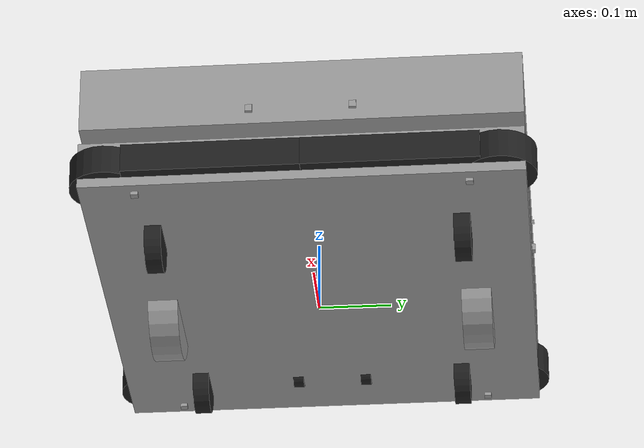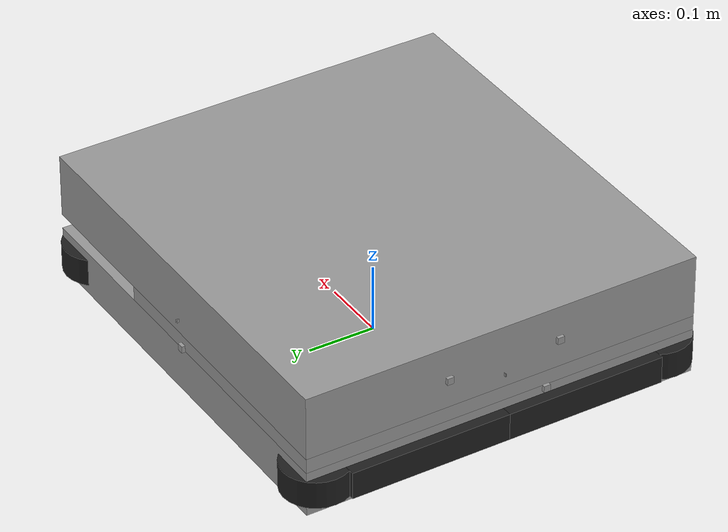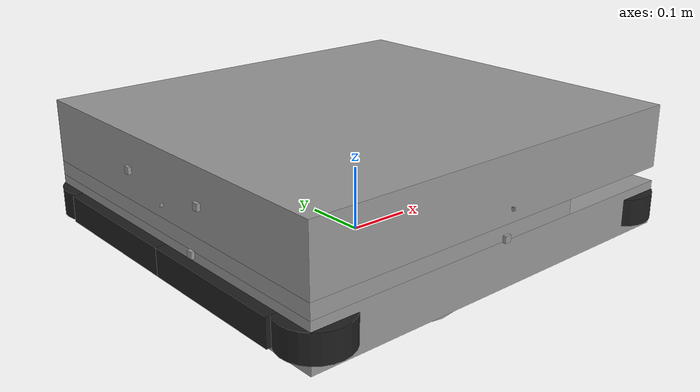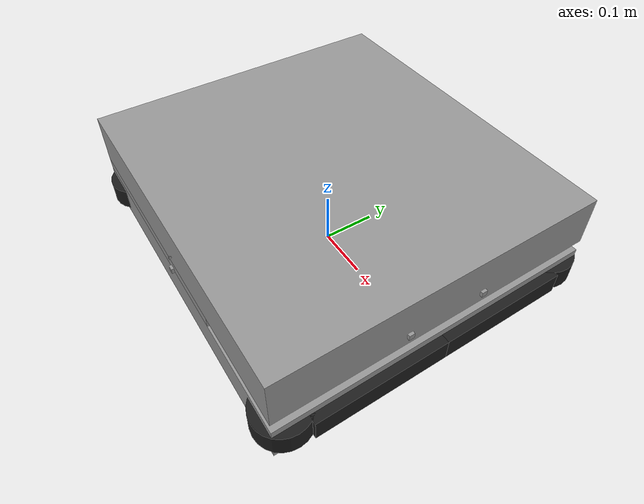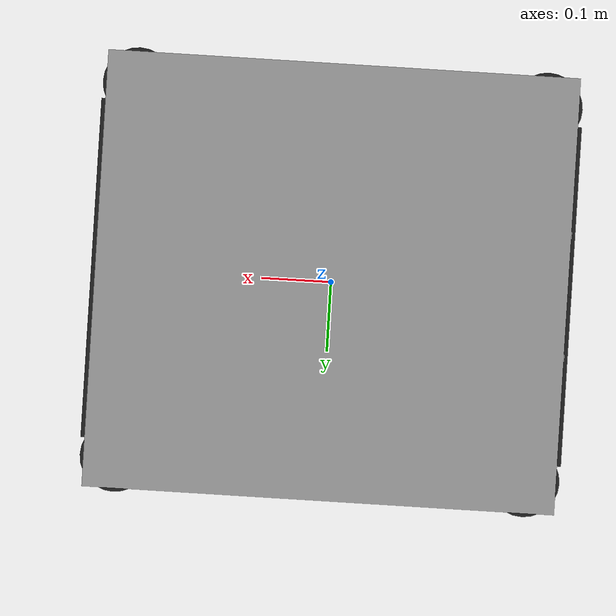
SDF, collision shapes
<sdf version='1.6'>
  <model name='gobot'>
    <link name='base_link'>
      <pose frame=''>0 0 0 0 -0 0</pose>
      <inertial>
        <pose frame=''>-0.020061 -6e-06 0.100401 0 -0 0</pose>
        <mass>10.025</mass>
        <inertia>
          <ixx>0.326514</ixx>
          <ixy>-1.9756e-05</ixy>
          <ixz>-0.00102117</ixz>
          <iyy>0.356993</iyy>
          <iyz>-1.32607e-06</iyz>
          <izz>0.336784</izz>
        </inertia>
      </inertial>
      <collision name='base_link_collision'>
        <pose frame=''>0 0 0.05 0 -0 0</pose>
        <geometry>
          <box>
            <size>0.648 0.599 0.068</size>
          </box>
        </geometry>
        <surface>
          <contact>
            <ode/>
          </contact>
          <friction>
            <ode/>
          </friction>
        </surface>
      </collision>
      <collision name='base_link_fixed_joint_lump__cliff_sensor_2_link_collision_1'>
        <pose frame=''>-0.304 -0.224 0.016 3.14159 1.57079 3.14159</pose>
        <geometry>
          <box>
            <size>0.01 0.01 0.01</size>
          </box>
        </geometry>
        <surface>
          <contact>
            <ode/>
          </contact>
          <friction>
            <ode/>
          </friction>
        </surface>
      </collision>
      <collision name='base_link_fixed_joint_lump__cliff_sensor_3_link_collision_2'>
        <pose frame=''>0.304 0.224 0.016 3.14159 1.57079 3.14159</pose>
        <geometry>
          <box>
            <size>0.01 0.01 0.01</size>
          </box>
        </geometry>
        <surface>
          <contact>
            <ode/>
          </contact>
          <friction>
            <ode/>
          </friction>
        </surface>
      </collision>
      <collision name='base_link_fixed_joint_lump__cliff_sensor_4_link_collision_3'>
        <pose frame=''>-0.304 0.224 0.016 3.14159 1.57079 3.14159</pose>
        <geometry>
          <box>
            <size>0.01 0.01 0.01</size>
          </box>
        </geometry>
        <surface>
          <contact>
            <ode/>
          </contact>
          <friction>
            <ode/>
          </friction>
        </surface>
      </collision>
      <collision name='base_link_fixed_joint_lump__cliff_sensor_link_collision_4'>
        <pose frame=''>0.304 -0.224 0.016 3.14159 1.57079 3.14159</pose>
        <geometry>
          <box>
            <size>0.01 0.01 0.01</size>
          </box>
        </geometry>
        <surface>
          <contact>
            <ode/>
          </contact>
          <friction>
            <ode/>
          </friction>
        </surface>
      </collision>
      <collision name='base_link_fixed_joint_lump__hokuyo_link_collision_5'>
        <pose frame=''>0.266 0 0.07 0 -0 0</pose>
        <geometry>
          <box>
            <size>0.02 0.02 0.06</size>
          </box>
        </geometry>
      </collision>
      <collision name='base_link_fixed_joint_lump__left_1_wall_link_collision_6'>
        <pose frame=''>0.000957 0.30181 0.126 0 -0 -0.392699</pose>
        <geometry>
          <box>
            <size>0.0001 0.005 0.005</size>
          </box>
        </geometry>
        <surface>
          <contact>
            <ode/>
          </contact>
          <friction>
            <ode/>
          </friction>
        </surface>
      </collision>
      <collision name='base_link_fixed_joint_lump__left_1_link_collision_7'>
        <pose frame=''>0.000883 0.30184 0.126 0 -0 -0.392699</pose>
        <geometry>
          <box>
            <size>1e-05 1e-05 1e-05</size>
          </box>
        </geometry>
        <surface>
          <contact>
            <ode/>
          </contact>
          <friction>
            <ode/>
          </friction>
        </surface>
      </collision>
      <collision name='base_link_fixed_joint_lump__left_2_wall_link_collision_8'>
        <pose frame=''>-0.000957 0.30181 0.126 0 -0 -2.74889</pose>
        <geometry>
          <box>
            <size>0.0001 0.005 0.005</size>
          </box>
        </geometry>
        <surface>
          <contact>
            <ode/>
          </contact>
          <friction>
            <ode/>
          </friction>
        </surface>
      </collision>
      <collision name='base_link_fixed_joint_lump__left_2_link_collision_9'>
        <pose frame=''>-0.000883 0.30184 0.126 0 -0 -2.74889</pose>
        <geometry>
          <box>
            <size>1e-05 1e-05 1e-05</size>
          </box>
        </geometry>
        <surface>
          <contact>
            <ode/>
          </contact>
          <friction>
            <ode/>
          </friction>
        </surface>
      </collision>
      <collision name='base_link_fixed_joint_lump__mid_base_link_collision_10'>
        <pose frame=''>-0.1 0 0.095 0 -0 0</pose>
        <geometry>
          <box>
            <size>0.448 0.599 0.022</size>
          </box>
        </geometry>
        <surface>
          <contact>
            <ode/>
          </contact>
          <friction>
            <ode/>
          </friction>
        </surface>
      </collision>
      <collision name='base_link_fixed_joint_lump__top_base_link_collision_11'>
        <pose frame=''>0 0 0.1535 0 -0 0</pose>
        <geometry>
          <box>
            <size>0.648 0.599 0.095</size>
          </box>
        </geometry>
        <surface>
          <contact>
            <ode/>
          </contact>
          <friction>
            <ode/>
          </friction>
        </surface>
      </collision>
      <collision name='base_link_fixed_joint_lump__prox_left_link_collision_12'>
        <pose frame=''>-0.324 0.085 0.15 0 -0 -3.14159</pose>
        <geometry>
          <box>
            <size>0.01 0.01 0.01</size>
          </box>
        </geometry>
        <surface>
          <contact>
            <ode/>
          </contact>
          <friction>
            <ode/>
          </friction>
        </surface>
      </collision>
      <collision name='base_link_fixed_joint_lump__prox_right_link_collision_13'>
        <pose frame=''>-0.324 -0.085 0.15 0 -0 -3.14159</pose>
        <geometry>
          <box>
            <size>0.01 0.01 0.01</size>
          </box>
        </geometry>
        <surface>
          <contact>
            <ode/>
          </contact>
          <friction>
            <ode/>
          </friction>
        </surface>
      </collision>
      <collision name='base_link_fixed_joint_lump__rear_1_wall_link_collision_14'>
        <pose frame=''>-0.326479 0.000326 0.126 0 -0 1.4399</pose>
        <geometry>
          <box>
            <size>0.0001 0.005 0.005</size>
          </box>
        </geometry>
        <surface>
          <contact>
            <ode/>
          </contact>
          <friction>
            <ode/>
          </friction>
        </surface>
      </collision>
      <collision name='base_link_fixed_joint_lump__rear_1_link_collision_15'>
        <pose frame=''>-0.326489 0.000247 0.126 0 -0 1.4399</pose>
        <geometry>
          <box>
            <size>1e-05 1e-05 1e-05</size>
          </box>
        </geometry>
        <surface>
          <contact>
            <ode/>
          </contact>
          <friction>
            <ode/>
          </friction>
        </surface>
      </collision>
      <collision name='base_link_fixed_joint_lump__rear_2_wall_link_collision_16'>
        <pose frame=''>-0.326479 -0.000326 0.126 0 0 -1.4399</pose>
        <geometry>
          <box>
            <size>0.0001 0.005 0.005</size>
          </box>
        </geometry>
        <surface>
          <contact>
            <ode/>
          </contact>
          <friction>
            <ode/>
          </friction>
        </surface>
      </collision>
      <collision name='base_link_fixed_joint_lump__rear_2_link_collision_17'>
        <pose frame=''>-0.326489 -0.000247 0.126 0 0 -1.4399</pose>
        <geometry>
          <box>
            <size>1e-05 1e-05 1e-05</size>
          </box>
        </geometry>
        <surface>
          <contact>
            <ode/>
          </contact>
          <friction>
            <ode/>
          </friction>
        </surface>
      </collision>
      <collision name='base_link_fixed_joint_lump__right_1_wall_link_collision_18'>
        <pose frame=''>-0.000957 -0.30181 0.126 0 -0 2.74889</pose>
        <geometry>
          <box>
            <size>0.0001 0.005 0.005</size>
          </box>
        </geometry>
        <surface>
          <contact>
            <ode/>
          </contact>
          <friction>
            <ode/>
          </friction>
        </surface>
      </collision>
      <collision name='base_link_fixed_joint_lump__right_1_link_collision_19'>
        <pose frame=''>-0.000883 -0.30184 0.126 0 -0 2.74889</pose>
        <geometry>
          <box>
            <size>1e-05 1e-05 1e-05</size>
          </box>
        </geometry>
        <surface>
          <contact>
            <ode/>
          </contact>
          <friction>
            <ode/>
          </friction>
        </surface>
      </collision>
      <collision name='base_link_fixed_joint_lump__right_2_wall_link_collision_20'>
        <pose frame=''>0.000957 -0.30181 0.126 0 -0 0.392699</pose>
        <geometry>
          <box>
            <size>0.0001 0.005 0.005</size>
          </box>
        </geometry>
        <surface>
          <contact>
            <ode/>
          </contact>
          <friction>
            <ode/>
          </friction>
        </surface>
      </collision>
      <collision name='base_link_fixed_joint_lump__right_2_link_collision_21'>
        <pose frame=''>0.000883 -0.30184 0.126 0 -0 0.392699</pose>
        <geometry>
          <box>
            <size>1e-05 1e-05 1e-05</size>
          </box>
        </geometry>
        <surface>
          <contact>
            <ode/>
          </contact>
          <friction>
            <ode/>
          </friction>
        </surface>
      </collision>
      <collision name='base_link_fixed_joint_lump__sonar_E0_link_collision_22'>
        <pose frame=''>-0.324 -0.065 0.08 0 -0 -3.14159</pose>
        <geometry>
          <box>
            <size>0.01 0.01 0.01</size>
          </box>
        </geometry>
        <surface>
          <contact>
            <ode/>
          </contact>
          <friction>
            <ode/>
          </friction>
        </surface>
      </collision>
      <collision name='base_link_fixed_joint_lump__sonar_E2_link_collision_23'>
        <pose frame=''>0.324 -0.07 0.128 0 -0 0</pose>
        <geometry>
          <box>
            <size>0.01 0.01 0.01</size>
          </box>
        </geometry>
        <surface>
          <contact>
            <ode/>
          </contact>
          <friction>
            <ode/>
          </friction>
        </surface>
      </collision>
      <collision name='base_link_fixed_joint_lump__sonar_E4_link_collision_24'>
        <pose frame=''>0.324 0.07 0.128 0 -0 0</pose>
        <geometry>
          <box>
            <size>0.01 0.01 0.01</size>
          </box>
        </geometry>
        <surface>
          <contact>
            <ode/>
          </contact>
          <friction>
            <ode/>
          </friction>
        </surface>
      </collision>
      <collision name='base_link_fixed_joint_lump__sonar_E6_link_collision_25'>
        <pose frame=''>-0.009 0.2995 0.088 0 -0 1.5708</pose>
        <geometry>
          <box>
            <size>0.01 0.01 0.01</size>
          </box>
        </geometry>
        <surface>
          <contact>
            <ode/>
          </contact>
          <friction>
            <ode/>
          </friction>
        </surface>
      </collision>
      <collision name='base_link_fixed_joint_lump__sonar_E8_link_collision_26'>
        <pose frame=''>-0.009 -0.2995 0.088 0 -0 -1.5708</pose>
        <geometry>
          <box>
            <size>0.01 0.01 0.01</size>
          </box>
        </geometry>
        <surface>
          <contact>
            <ode/>
          </contact>
          <friction>
            <ode/>
          </friction>
        </surface>
      </collision>
      <visual name='base_link_visual'>
        <pose frame=''>0 0 0.05 0 -0 0</pose>
        <geometry>
          <box>
            <size>0.648 0.599 0.068</size>
          </box>
        </geometry>
        <material>
          <script>
            <name>Gazebo/Grey</name>
            <uri>file://media/materials/scripts/gazebo.material</uri>
          </script>
        </material>
      </visual>
      <visual name='base_link_fixed_joint_lump__cliff_sensor_2_link_visual_1'>
        <pose frame=''>-0.304 -0.224 0.016 3.14159 1.57079 3.14159</pose>
        <geometry>
          <mesh>
            <scale>1 1 1</scale>
            <uri>model://hector_sensors_description/meshes/sonar_sensor/max_sonar_ez4.dae</uri>
          </mesh>
        </geometry>
        <material>
          <script>
            <uri>__default__</uri>
            <name>__default__</name>
          </script>
        </material>
      </visual>
      <visual name='base_link_fixed_joint_lump__cliff_sensor_3_link_visual_2'>
        <pose frame=''>0.304 0.224 0.016 3.14159 1.57079 3.14159</pose>
        <geometry>
          <mesh>
            <scale>1 1 1</scale>
            <uri>model://hector_sensors_description/meshes/sonar_sensor/max_sonar_ez4.dae</uri>
          </mesh>
        </geometry>
        <material>
          <script>
            <uri>__default__</uri>
            <name>__default__</name>
          </script>
        </material>
      </visual>
      <visual name='base_link_fixed_joint_lump__cliff_sensor_4_link_visual_3'>
        <pose frame=''>-0.304 0.224 0.016 3.14159 1.57079 3.14159</pose>
        <geometry>
          <mesh>
            <scale>1 1 1</scale>
            <uri>model://hector_sensors_description/meshes/sonar_sensor/max_sonar_ez4.dae</uri>
          </mesh>
        </geometry>
        <material>
          <script>
            <uri>__default__</uri>
            <name>__default__</name>
          </script>
        </material>
      </visual>
      <visual name='base_link_fixed_joint_lump__cliff_sensor_link_visual_4'>
        <pose frame=''>0.304 -0.224 0.016 3.14159 1.57079 3.14159</pose>
        <geometry>
          <mesh>
            <scale>1 1 1</scale>
            <uri>model://hector_sensors_description/meshes/sonar_sensor/max_sonar_ez4.dae</uri>
          </mesh>
        </geometry>
        <material>
          <script>
            <uri>__default__</uri>
            <name>__default__</name>
          </script>
        </material>
      </visual>
      <visual name='base_link_fixed_joint_lump__hokuyo_link_visual_5'>
        <pose frame=''>0.266 0 0.04 0 -0 0</pose>
        <geometry>
          <mesh>
            <scale>0.024 0.024 0.024</scale>
            <uri>/home/m-a/catkin_ws/src/gobot_simulation/gobot_description/meshes/hokuyo.dae</uri>
          </mesh>
        </geometry>
      </visual>
      <visual name='base_link_fixed_joint_lump__left_1_wall_link_visual_6'>
        <pose frame=''>0.000957 0.30181 0.126 0 -0 -0.392699</pose>
        <geometry>
          <box>
            <size>0.0001 0.005 0.005</size>
          </box>
        </geometry>
        <material>
          <script>
            <name>Gazebo/Grey</name>
            <uri>file://media/materials/scripts/gazebo.material</uri>
          </script>
        </material>
      </visual>
      <visual name='base_link_fixed_joint_lump__left_1_link_visual_7'>
        <pose frame=''>0.000883 0.30184 0.126 0 -0 -0.392699</pose>
        <geometry>
          <box>
            <size>1e-05 1e-05 1e-05</size>
          </box>
        </geometry>
        <material>
          <script>
            <name>Gazebo/White</name>
            <uri>file://media/materials/scripts/gazebo.material</uri>
          </script>
        </material>
      </visual>
      <visual name='base_link_fixed_joint_lump__left_2_wall_link_visual_8'>
        <pose frame=''>-0.000957 0.30181 0.126 0 -0 -2.74889</pose>
        <geometry>
          <box>
            <size>0.0001 0.005 0.005</size>
          </box>
        </geometry>
        <material>
          <script>
            <name>Gazebo/Grey</name>
            <uri>file://media/materials/scripts/gazebo.material</uri>
          </script>
        </material>
      </visual>
      <visual name='base_link_fixed_joint_lump__left_2_link_visual_9'>
        <pose frame=''>-0.000883 0.30184 0.126 0 -0 -2.74889</pose>
        <geometry>
          <box>
            <size>1e-05 1e-05 1e-05</size>
          </box>
        </geometry>
        <material>
          <script>
            <name>Gazebo/White</name>
            <uri>file://media/materials/scripts/gazebo.material</uri>
          </script>
        </material>
      </visual>
      <visual name='base_link_fixed_joint_lump__mid_base_link_visual_10'>
        <pose frame=''>-0.1 0 0.095 0 -0 0</pose>
        <geometry>
          <box>
            <size>0.448 0.599 0.022</size>
          </box>
        </geometry>
        <material>
          <script>
            <name>Gazebo/Grey</name>
            <uri>file://media/materials/scripts/gazebo.material</uri>
          </script>
        </material>
      </visual>
      <visual name='base_link_fixed_joint_lump__top_base_link_visual_11'>
        <pose frame=''>0 0 0.1535 0 -0 0</pose>
        <geometry>
          <box>
            <size>0.648 0.599 0.095</size>
          </box>
        </geometry>
        <material>
          <script>
            <name>Gazebo/Grey</name>
            <uri>file://media/materials/scripts/gazebo.material</uri>
          </script>
        </material>
      </visual>
      <visual name='base_link_fixed_joint_lump__prox_left_link_visual_12'>
        <pose frame=''>-0.324 0.085 0.15 0 -0 -3.14159</pose>
        <geometry>
          <mesh>
            <scale>1 1 1</scale>
            <uri>model://hector_sensors_description/meshes/sonar_sensor/max_sonar_ez4.dae</uri>
          </mesh>
        </geometry>
        <material>
          <script>
            <uri>__default__</uri>
            <name>__default__</name>
          </script>
        </material>
      </visual>
      <visual name='base_link_fixed_joint_lump__prox_right_link_visual_13'>
        <pose frame=''>-0.324 -0.085 0.15 0 -0 -3.14159</pose>
        <geometry>
          <mesh>
            <scale>1 1 1</scale>
            <uri>model://hector_sensors_description/meshes/sonar_sensor/max_sonar_ez4.dae</uri>
          </mesh>
        </geometry>
        <material>
          <script>
            <uri>__default__</uri>
            <name>__default__</name>
          </script>
        </material>
      </visual>
      <visual name='base_link_fixed_joint_lump__rear_1_wall_link_visual_14'>
        <pose frame=''>-0.326479 0.000326 0.126 0 -0 1.4399</pose>
        <geometry>
          <box>
            <size>0.0001 0.005 0.005</size>
          </box>
        </geometry>
        <material>
          <script>
            <name>Gazebo/Grey</name>
            <uri>file://media/materials/scripts/gazebo.material</uri>
          </script>
        </material>
      </visual>
      <visual name='base_link_fixed_joint_lump__rear_1_link_visual_15'>
        <pose frame=''>-0.326489 0.000247 0.126 0 -0 1.4399</pose>
        <geometry>
          <box>
            <size>1e-05 1e-05 1e-05</size>
          </box>
        </geometry>
        <material>
          <script>
            <name>Gazebo/White</name>
            <uri>file://media/materials/scripts/gazebo.material</uri>
          </script>
        </material>
      </visual>
      <visual name='base_link_fixed_joint_lump__rear_2_wall_link_visual_16'>
        <pose frame=''>-0.326479 -0.000326 0.126 0 0 -1.4399</pose>
        <geometry>
          <box>
            <size>0.0001 0.005 0.005</size>
          </box>
        </geometry>
        <material>
          <script>
            <name>Gazebo/Grey</name>
            <uri>file://media/materials/scripts/gazebo.material</uri>
          </script>
        </material>
      </visual>
      <visual name='base_link_fixed_joint_lump__rear_2_link_visual_17'>
        <pose frame=''>-0.326489 -0.000247 0.126 0 0 -1.4399</pose>
        <geometry>
          <box>
            <size>1e-05 1e-05 1e-05</size>
          </box>
        </geometry>
        <material>
          <script>
            <name>Gazebo/White</name>
            <uri>file://media/materials/scripts/gazebo.material</uri>
          </script>
        </material>
      </visual>
      <visual name='base_link_fixed_joint_lump__right_1_wall_link_visual_18'>
        <pose frame=''>-0.000957 -0.30181 0.126 0 -0 2.74889</pose>
        <geometry>
          <box>
            <size>0.0001 0.005 0.005</size>
          </box>
        </geometry>
        <material>
          <script>
            <name>Gazebo/Grey</name>
            <uri>file://media/materials/scripts/gazebo.material</uri>
          </script>
        </material>
      </visual>
      <visual name='base_link_fixed_joint_lump__right_1_link_visual_19'>
        <pose frame=''>-0.000883 -0.30184 0.126 0 -0 2.74889</pose>
        <geometry>
          <box>
            <size>1e-05 1e-05 1e-05</size>
          </box>
        </geometry>
        <material>
          <script>
            <name>Gazebo/White</name>
            <uri>file://media/materials/scripts/gazebo.material</uri>
          </script>
        </material>
      </visual>
      <visual name='base_link_fixed_joint_lump__right_2_wall_link_visual_20'>
        <pose frame=''>0.000957 -0.30181 0.126 0 -0 0.392699</pose>
        <geometry>
          <box>
            <size>0.0001 0.005 0.005</size>
          </box>
        </geometry>
        <material>
          <script>
            <name>Gazebo/Grey</name>
            <uri>file://media/materials/scripts/gazebo.material</uri>
          </script>
        </material>
      </visual>
      <visual name='base_link_fixed_joint_lump__right_2_link_visual_21'>
        <pose frame=''>0.000883 -0.30184 0.126 0 -0 0.392699</pose>
        <geometry>
          <box>
            <size>1e-05 1e-05 1e-05</size>
          </box>
        </geometry>
        <material>
          <script>
            <name>Gazebo/White</name>
            <uri>file://media/materials/scripts/gazebo.material</uri>
          </script>
        </material>
      </visual>
      <visual name='base_link_fixed_joint_lump__sonar_E0_link_visual_22'>
        <pose frame=''>-0.324 -0.065 0.08 0 -0 -3.14159</pose>
        <geometry>
          <mesh>
            <scale>1 1 1</scale>
            <uri>model://hector_sensors_description/meshes/sonar_sensor/max_sonar_ez4.dae</uri>
          </mesh>
        </geometry>
        <material>
          <script>
            <uri>__default__</uri>
            <name>__default__</name>
          </script>
        </material>
      </visual>
      <visual name='base_link_fixed_joint_lump__sonar_E2_link_visual_23'>
        <pose frame=''>0.324 -0.07 0.128 0 -0 0</pose>
        <geometry>
          <mesh>
            <scale>1 1 1</scale>
            <uri>model://hector_sensors_description/meshes/sonar_sensor/max_sonar_ez4.dae</uri>
          </mesh>
        </geometry>
        <material>
          <script>
            <uri>__default__</uri>
            <name>__default__</name>
          </script>
        </material>
      </visual>
      <visual name='base_link_fixed_joint_lump__sonar_E4_link_visual_24'>
        <pose frame=''>0.324 0.07 0.128 0 -0 0</pose>
        <geometry>
          <mesh>
            <scale>1 1 1</scale>
            <uri>model://hector_sensors_description/meshes/sonar_sensor/max_sonar_ez4.dae</uri>
          </mesh>
        </geometry>
        <material>
          <script>
            <uri>__default__</uri>
            <name>__default__</name>
          </script>
        </material>
      </visual>
      <visual name='base_link_fixed_joint_lump__sonar_E6_link_visual_25'>
        <pose frame=''>-0.009 0.2995 0.088 0 -0 1.5708</pose>
        <geometry>
          <mesh>
            <scale>1 1 1</scale>
            <uri>model://hector_sensors_description/meshes/sonar_sensor/max_sonar_ez4.dae</uri>
          </mesh>
        </geometry>
        <material>
          <script>
            <uri>__default__</uri>
            <name>__default__</name>
          </script>
        </material>
      </visual>
      <visual name='base_link_fixed_joint_lump__sonar_E8_link_visual_26'>
        <pose frame=''>-0.009 -0.2995 0.088 0 -0 -1.5708</pose>
        <geometry>
          <mesh>
            <scale>1 1 1</scale>
            <uri>model://hector_sensors_description/meshes/sonar_sensor/max_sonar_ez4.dae</uri>
          </mesh>
        </geometry>
        <material>
          <script>
            <uri>__default__</uri>
            <name>__default__</name>
          </script>
        </material>
      </visual>
      <velocity_decay/>
      <velocity_decay/>
      <sensor name='cliff_sensor_2' type='ray'>
        <always_on>1</always_on>
        <update_rate>10</update_rate>
        <visualize>1</visualize>
        <ray>
          <scan>
            <horizontal>
              <samples>1</samples>
              <resolution>1</resolution>
              <min_angle>-0.025</min_angle>
              <max_angle>0.025</max_angle>
            </horizontal>
          </scan>
          <range>
            <min>0.01</min>
            <max>2</max>
            <resolution>0.01</resolution>
          </range>
        </ray>
        <plugin name='gazebo_ros_cliff_sensor_2_controller' filename='libhector_gazebo_ros_sonar.so'>
          <gaussianNoise>0.03</gaussianNoise>
          <topicName>cliff_sensor_2_topic</topicName>
          <frameId>cliff_sensor_2_link</frameId>
        </plugin>
        <pose frame=''>-0.304 -0.224 0.016 3.14159 1.57079 3.14159</pose>
      </sensor>
      <velocity_decay/>
      <sensor name='cliff_sensor_3' type='ray'>
        <always_on>1</always_on>
        <update_rate>10</update_rate>
        <visualize>1</visualize>
        <ray>
          <scan>
            <horizontal>
              <samples>1</samples>
              <resolution>1</resolution>
              <min_angle>-0.025</min_angle>
              <max_angle>0.025</max_angle>
            </horizontal>
          </scan>
          <range>
            <min>0.01</min>
            <max>2</max>
            <resolution>0.01</resolution>
          </range>
        </ray>
        <plugin name='gazebo_ros_cliff_sensor_3_controller' filename='libhector_gazebo_ros_sonar.so'>
          <gaussianNoise>0.03</gaussianNoise>
          <topicName>cliff_sensor_3_topic</topicName>
          <frameId>cliff_sensor_3_link</frameId>
        </plugin>
        <pose frame=''>0.304 0.224 0.016 3.14159 1.57079 3.14159</pose>
      </sensor>
      <velocity_decay/>
      <sensor name='cliff_sensor_4' type='ray'>
        <always_on>1</always_on>
        <update_rate>10</update_rate>
        <visualize>1</visualize>
        <ray>
          <scan>
            <horizontal>
              <samples>1</samples>
              <resolution>1</resolution>
              <min_angle>-0.025</min_angle>
              <max_angle>0.025</max_angle>
            </horizontal>
          </scan>
          <range>
            <min>0.01</min>
            <max>2</max>
            <resolution>0.01</resolution>
          </range>
        </ray>
        <plugin name='gazebo_ros_cliff_sensor_4_controller' filename='libhector_gazebo_ros_sonar.so'>
          <gaussianNoise>0.03</gaussianNoise>
          <topicName>cliff_sensor_4_topic</topicName>
          <frameId>cliff_sensor_4_link</frameId>
        </plugin>
        <pose frame=''>-0.304 0.224 0.016 3.14159 1.57079 3.14159</pose>
      </sensor>
      <velocity_decay/>
      <sensor name='cliff_sensor' type='ray'>
        <always_on>1</always_on>
        <update_rate>10</update_rate>
        <visualize>1</visualize>
        <ray>
          <scan>
            <horizontal>
              <samples>1</samples>
              <resolution>1</resolution>
              <min_angle>-0.025</min_angle>
              <max_angle>0.025</max_angle>
            </horizontal>
          </scan>
          <range>
            <min>0.03</min>
            <max>2</max>
            <resolution>0.01</resolution>
          </range>
        </ray>
        <plugin name='gazebo_ros_cliff_sensor_controller' filename='libhector_gazebo_ros_sonar.so'>
          <gaussianNoise>0.03</gaussianNoise>
          <topicName>cliff_sensor_topic</topicName>
          <frameId>cliff_sensor_link</frameId>
        </plugin>
        <pose frame=''>0.304 -0.224 0.016 3.14159 1.57079 3.14159</pose>
      </sensor>
      <velocity_decay/>
      <sensor name='hokuyo_laser' type='ray'>
        <always_on>1</always_on>
        <update_rate>20</update_rate>
        <visualize>1</visualize>
        <ray>
          <scan>
            <horizontal>
              <samples>640</samples>
              <resolution>1</resolution>
              <min_angle>-1.5708</min_angle>
              <max_angle>1.5708</max_angle>
            </horizontal>
          </scan>
          <range>
            <min>0.02</min>
            <max>4</max>
            <resolution>0.03</resolution>
          </range>
          <noise>
            <type>gaussian</type>
            <mean>0</mean>
            <stddev>0.01</stddev>
          </noise>
        </ray>
        <plugin name='gazebo_ros_hokuyo_laser_controller' filename='libgazebo_ros_laser.so'>
          <alwaysOn>true</alwaysOn>
          <updateRate>20</updateRate>
          <topicName>/scan</topicName>
          <frameName>hokuyo_link</frameName>
        </plugin>
        <pose frame=''>0.268 0 0.0925 0 -0 0</pose>
      </sensor>
      <velocity_decay/>
      <velocity_decay/>
      <sensor name='camera' type='camera'>
        <camera name='__default__'>
          <horizontal_fov>0.1</horizontal_fov>
          <image>
            <width>1</width>
            <height>1</height>
          </image>
          <clip>
            <near>1e-05</near>
            <far>100</far>
          </clip>
        </camera>
        <plugin name='ir_controller' filename='libgazebo_ros_camera.so'>
          <cameraName>left_1_camera</cameraName>
          <alwaysOn>true</alwaysOn>
          <updateRate>10</updateRate>
          <imageTopicName>rgb/image_raw</imageTopicName>
          <cameraInfoTopicName>rgb/camera_info</cameraInfoTopicName>
          <frameName>left_1_link</frameName>
          <hackBaseline>0.07</hackBaseline>
          <distortionK1>0.0</distortionK1>
          <distortionK2>0.0</distortionK2>
          <distortionK3>0.0</distortionK3>
          <distortionT1>0.0</distortionT1>
          <distortionT2>0.0</distortionT2>
        </plugin>
        <pose frame=''>0.000883 0.30184 0.126 0 -0 -0.392699</pose>
      </sensor>
      <velocity_decay/>
      <velocity_decay/>
      <sensor name='camera' type='camera'>
        <camera name='__default__'>
          <horizontal_fov>0.1</horizontal_fov>
          <image>
            <width>1</width>
            <height>1</height>
          </image>
          <clip>
            <near>1e-05</near>
            <far>100</far>
          </clip>
        </camera>
        <plugin name='ir_controller' filename='libgazebo_ros_camera.so'>
          <cameraName>left_2_camera</cameraName>
          <alwaysOn>true</alwaysOn>
          <updateRate>10</updateRate>
          <imageTopicName>rgb/image_raw</imageTopicName>
          <cameraInfoTopicName>rgb/camera_info</cameraInfoTopicName>
          <frameName>left_2_link</frameName>
          <hackBaseline>0.07</hackBaseline>
          <distortionK1>0.0</distortionK1>
          <distortionK2>0.0</distortionK2>
          <distortionK3>0.0</distortionK3>
          <distortionT1>0.0</distortionT1>
          <distortionT2>0.0</distortionT2>
        </plugin>
        <pose frame=''>-0.000883 0.30184 0.126 0 -0 -2.74889</pose>
      </sensor>
      <velocity_decay/>
      <velocity_decay/>
      <velocity_decay/>
      <sensor name='prox_left' type='ray'>
        <always_on>1</always_on>
        <update_rate>20</update_rate>
        <visualize>1</visualize>
        <ray>
          <scan>
            <horizontal>
              <samples>1</samples>
              <resolution>1</resolution>
              <min_angle>-0.025</min_angle>
              <max_angle>0.025</max_angle>
            </horizontal>
          </scan>
          <range>
            <min>0.05</min>
            <max>0.15</max>
            <resolution>0.01</resolution>
          </range>
        </ray>
        <plugin name='gazebo_ros_prox_left_controller' filename='libhector_gazebo_ros_sonar.so'>
          <gaussianNoise>0.0</gaussianNoise>
          <topicName>/sensors/sonar_sensor/proximity_left</topicName>
          <frameId>prox_left_link</frameId>
        </plugin>
        <pose frame=''>-0.324 0.085 0.15 0 -0 -3.14159</pose>
      </sensor>
      <velocity_decay/>
      <sensor name='prox_right' type='ray'>
        <always_on>1</always_on>
        <update_rate>20</update_rate>
        <visualize>1</visualize>
        <ray>
          <scan>
            <horizontal>
              <samples>1</samples>
              <resolution>1</resolution>
              <min_angle>-0.025</min_angle>
              <max_angle>0.025</max_angle>
            </horizontal>
          </scan>
          <range>
            <min>0.05</min>
            <max>0.15</max>
            <resolution>0.01</resolution>
          </range>
        </ray>
        <plugin name='gazebo_ros_prox_right_controller' filename='libhector_gazebo_ros_sonar.so'>
          <gaussianNoise>0.0</gaussianNoise>
          <topicName>/sensors/sonar_sensor/proximity_right</topicName>
          <frameId>prox_right_link</frameId>
        </plugin>
        <pose frame=''>-0.324 -0.085 0.15 0 -0 -3.14159</pose>
      </sensor>
      <velocity_decay/>
      <velocity_decay/>
      <sensor name='camera' type='camera'>
        <camera name='__default__'>
          <horizontal_fov>0.1</horizontal_fov>
          <image>
            <width>1</width>
            <height>1</height>
          </image>
          <clip>
            <near>1e-05</near>
            <far>100</far>
          </clip>
        </camera>
        <plugin name='ir_controller' filename='libgazebo_ros_camera.so'>
          <cameraName>rear_1_camera</cameraName>
          <alwaysOn>true</alwaysOn>
          <updateRate>10</updateRate>
          <imageTopicName>rgb/image_raw</imageTopicName>
          <cameraInfoTopicName>rgb/camera_info</cameraInfoTopicName>
          <frameName>rear_1_link</frameName>
          <hackBaseline>0.07</hackBaseline>
          <distortionK1>0.0</distortionK1>
          <distortionK2>0.0</distortionK2>
          <distortionK3>0.0</distortionK3>
          <distortionT1>0.0</distortionT1>
          <distortionT2>0.0</distortionT2>
        </plugin>
        <pose frame=''>-0.326489 0.000247 0.126 0 -0 1.4399</pose>
      </sensor>
      <velocity_decay/>
      <velocity_decay/>
      <sensor name='camera' type='camera'>
        <camera name='__default__'>
          <horizontal_fov>0.1</horizontal_fov>
          <image>
            <width>1</width>
            <height>1</height>
          </image>
          <clip>
            <near>1e-05</near>
            <far>100</far>
          </clip>
        </camera>
        <plugin name='ir_controller' filename='libgazebo_ros_camera.so'>
          <cameraName>rear_2_camera</cameraName>
          <alwaysOn>true</alwaysOn>
          <updateRate>10</updateRate>
          <imageTopicName>rgb/image_raw</imageTopicName>
          <cameraInfoTopicName>rgb/camera_info</cameraInfoTopicName>
          <frameName>rear_2_link</frameName>
          <hackBaseline>0.07</hackBaseline>
          <distortionK1>0.0</distortionK1>
          <distortionK2>0.0</distortionK2>
          <distortionK3>0.0</distortionK3>
          <distortionT1>0.0</distortionT1>
          <distortionT2>0.0</distortionT2>
        </plugin>
        <pose frame=''>-0.326489 -0.000247 0.126 0 0 -1.4399</pose>
      </sensor>
      <velocity_decay/>
      <velocity_decay/>
      <sensor name='camera' type='camera'>
        <camera name='__default__'>
          <horizontal_fov>0.1</horizontal_fov>
          <image>
            <width>1</width>
            <height>1</height>
          </image>
          <clip>
            <near>1e-05</near>
            <far>100</far>
          </clip>
        </camera>
        <plugin name='ir_controller' filename='libgazebo_ros_camera.so'>
          <cameraName>right_1_camera</cameraName>
          <alwaysOn>true</alwaysOn>
          <updateRate>10</updateRate>
          <imageTopicName>rgb/image_raw</imageTopicName>
          <cameraInfoTopicName>rgb/camera_info</cameraInfoTopicName>
          <frameName>right_1_link</frameName>
          <hackBaseline>0.07</hackBaseline>
          <distortionK1>0.0</distortionK1>
          <distortionK2>0.0</distortionK2>
          <distortionK3>0.0</distortionK3>
          <distortionT1>0.0</distortionT1>
          <distortionT2>0.0</distortionT2>
        </plugin>
        <pose frame=''>-0.000883 -0.30184 0.126 0 -0 2.74889</pose>
      </sensor>
      <velocity_decay/>
      <velocity_decay/>
      <sensor name='camera' type='camera'>
        <camera name='__default__'>
          <horizontal_fov>0.1</horizontal_fov>
          <image>
            <width>1</width>
            <height>1</height>
          </image>
          <clip>
            <near>1e-05</near>
            <far>100</far>
          </clip>
        </camera>
        <plugin name='ir_controller' filename='libgazebo_ros_camera.so'>
          <cameraName>right_2_camera</cameraName>
          <alwaysOn>true</alwaysOn>
          <updateRate>10</updateRate>
          <imageTopicName>rgb/image_raw</imageTopicName>
          <cameraInfoTopicName>rgb/camera_info</cameraInfoTopicName>
          <frameName>right_2_link</frameName>
          <hackBaseline>0.07</hackBaseline>
          <distortionK1>0.0</distortionK1>
          <distortionK2>0.0</distortionK2>
          <distortionK3>0.0</distortionK3>
          <distortionT1>0.0</distortionT1>
          <distortionT2>0.0</distortionT2>
        </plugin>
        <pose frame=''>0.000883 -0.30184 0.126 0 -0 0.392699</pose>
      </sensor>
      <velocity_decay/>
      <sensor name='sonar_E0' type='ray'>
        <always_on>1</always_on>
        <update_rate>20</update_rate>
        <visualize>0</visualize>
        <ray>
          <scan>
            <horizontal>
              <samples>60</samples>
              <resolution>1</resolution>
              <min_angle>-0.5236</min_angle>
              <max_angle>0.5236</max_angle>
            </horizontal>
          </scan>
          <range>
            <min>0.15</min>
            <max>6</max>
            <resolution>0.03</resolution>
          </range>
        </ray>
        <plugin name='gazebo_ros_sonar_E0_controller' filename='libhector_gazebo_ros_sonar.so'>
          <gaussianNoise>0.03</gaussianNoise>
          <topicName>/sensors/sonar_sensor/sonar_zero_range</topicName>
          <frameId>sonar_E0_link</frameId>
        </plugin>
        <pose frame=''>-0.324 -0.065 0.08 0 -0 -3.14159</pose>
      </sensor>
      <velocity_decay/>
      <sensor name='sonar_E2' type='ray'>
        <always_on>1</always_on>
        <update_rate>20</update_rate>
        <visualize>0</visualize>
        <ray>
          <scan>
            <horizontal>
              <samples>60</samples>
              <resolution>1</resolution>
              <min_angle>-0.5236</min_angle>
              <max_angle>0.5236</max_angle>
            </horizontal>
          </scan>
          <range>
            <min>0.15</min>
            <max>6</max>
            <resolution>0.03</resolution>
          </range>
        </ray>
        <plugin name='gazebo_ros_sonar_E2_controller' filename='libhector_gazebo_ros_sonar.so'>
          <gaussianNoise>0.03</gaussianNoise>
          <topicName>/sensors/sonar_sensor/sonar_two_range</topicName>
          <frameId>sonar_E2_link</frameId>
        </plugin>
        <pose frame=''>0.324 -0.07 0.128 0 -0 0</pose>
      </sensor>
      <velocity_decay/>
      <sensor name='sonar_E4' type='ray'>
        <always_on>1</always_on>
        <update_rate>20</update_rate>
        <visualize>0</visualize>
        <ray>
          <scan>
            <horizontal>
              <samples>60</samples>
              <resolution>1</resolution>
              <min_angle>-0.5236</min_angle>
              <max_angle>0.5236</max_angle>
            </horizontal>
          </scan>
          <range>
            <min>0.15</min>
            <max>6</max>
            <resolution>0.03</resolution>
          </range>
        </ray>
        <plugin name='gazebo_ros_sonar_E4_controller' filename='libhector_gazebo_ros_sonar.so'>
          <gaussianNoise>0.03</gaussianNoise>
          <topicName>/sensors/sonar_sensor/sonar_four_range</topicName>
          <frameId>sonar_E4_link</frameId>
        </plugin>
        <pose frame=''>0.324 0.07 0.128 0 -0 0</pose>
      </sensor>
      <velocity_decay/>
      <sensor name='sonar_E6' type='ray'>
        <always_on>1</always_on>
        <update_rate>20</update_rate>
        <visualize>0</visualize>
        <ray>
          <scan>
            <horizontal>
              <samples>60</samples>
              <resolution>1</resolution>
              <min_angle>-0.5236</min_angle>
              <max_angle>0.5236</max_angle>
            </horizontal>
          </scan>
          <range>
            <min>0.15</min>
            <max>6</max>
            <resolution>0.03</resolution>
          </range>
        </ray>
        <plugin name='gazebo_ros_sonar_E6_controller' filename='libhector_gazebo_ros_sonar.so'>
          <gaussianNoise>0.03</gaussianNoise>
          <topicName>/sensors/sonar_sensor/sonar_six_range</topicName>
          <frameId>sonar_E6_link</frameId>
        </plugin>
        <pose frame=''>-0.009 0.2995 0.088 0 -0 1.5708</pose>
      </sensor>
      <gravity>1</gravity>
      <velocity_decay/>
      <self_collide>0</self_collide>
      <sensor name='sonar_E8' type='ray'>
        <always_on>1</always_on>
        <update_rate>20</update_rate>
        <visualize>0</visualize>
        <ray>
          <scan>
            <horizontal>
              <samples>60</samples>
              <resolution>1</resolution>
              <min_angle>-0.5236</min_angle>
              <max_angle>0.5236</max_angle>
            </horizontal>
          </scan>
          <range>
            <min>0.15</min>
            <max>6</max>
            <resolution>0.03</resolution>
          </range>
        </ray>
        <plugin name='gazebo_ros_sonar_E8_controller' filename='libhector_gazebo_ros_sonar.so'>
          <gaussianNoise>0.03</gaussianNoise>
          <topicName>/sensors/sonar_sensor/sonar_eight_range</topicName>
          <frameId>sonar_E8_link</frameId>
        </plugin>
        <pose frame=''>-0.009 -0.2995 0.088 0 -0 -1.5708</pose>
      </sensor>
    </link>
    <link name='back_left_bumper'>
      <pose frame=''>-0.332 0.12 0.05 0 -0 0</pose>
      <inertial>
        <pose frame=''>0 0 0 0 -0 0</pose>
        <mass>0.4</mass>
        <inertia>
          <ixx>0.00197603</ixx>
          <ixy>0</ixy>
          <ixz>0</ixz>
          <iyy>6.45667e-05</iyy>
          <iyz>0</iyz>
          <izz>6.45667e-05</izz>
        </inertia>
      </inertial>
      <collision name='back_left_bumper_collision'>
        <pose frame=''>0 0 0 0 -0 0</pose>
        <geometry>
          <box>
            <size>0.016 0.24 0.041</size>
          </box>
        </geometry>
        <surface>
          <contact>
            <ode/>
          </contact>
          <friction>
            <ode/>
          </friction>
        </surface>
      </collision>
      <visual name='back_left_bumper_visual'>
        <pose frame=''>0 0 0 0 -0 0</pose>
        <geometry>
          <box>
            <size>0.016 0.24 0.041</size>
          </box>
        </geometry>
        <material>
          <script>
            <name>Gazebo/Black</name>
            <uri>file://media/materials/scripts/gazebo.material</uri>
          </script>
        </material>
      </visual>
      <gravity>1</gravity>
      <velocity_decay/>
      <self_collide>0</self_collide>
      <sensor name='back_left_bumper_sensor' type='contact'>
        <contact>
          <collision>base_link_fixed_joint_lump__back_left_bumper_collision_1</collision>
          <topic>__default_topic__</topic>
        </contact>
        <plugin name='back_left_bumper_gazebo_ros_bumper_controller' filename='libgazebo_ros_bumper.so'>
          <alwaysOn>true</alwaysOn>
          <updateRate>20</updateRate>
          <bumperTopicName>back_left_bumper</bumperTopicName>
          <frameName>world</frameName>
        </plugin>
      </sensor>
    </link>
    <joint name='back_left_bumper_joint' type='prismatic'>
      <child>back_left_bumper</child>
      <parent>base_link</parent>
      <axis>
        <xyz>1 0 0</xyz>
        <limit>
          <lower>0</lower>
          <upper>0.005</upper>
          <effort>1000</effort>
          <velocity>-0.5</velocity>
        </limit>
        <dynamics>
          <spring_reference>0</spring_reference>
          <spring_stiffness>0</spring_stiffness>
        </dynamics>
        <use_parent_model_frame>1</use_parent_model_frame>
      </axis>
    </joint>
    <link name='back_left_caster_wheel'>
      <pose frame=''>-0.244 0.1895 0.011 0 -0 0</pose>
      <inertial>
        <pose frame=''>0 0 0 0 -0 0</pose>
        <mass>0.2</mass>
        <inertia>
          <ixx>7.72667e-05</ixx>
          <ixy>0</ixy>
          <ixz>0</ixz>
          <iyy>7.72667e-05</iyy>
          <iyz>0</iyz>
          <izz>0.0001369</izz>
        </inertia>
      </inertial>
      <collision name='back_left_caster_wheel_collision'>
        <pose frame=''>0 0 0 1.5708 -0 0</pose>
        <geometry>
          <cylinder>
            <length>0.023</length>
            <radius>0.037</radius>
          </cylinder>
        </geometry>
        <surface>
          <contact>
            <ode>
              <kp>1e+07</kp>
              <kd>1</kd>
            </ode>
          </contact>
          <friction>
            <ode>
              <mu>0</mu>
              <mu2>0</mu2>
              <fdir1>1 0 0</fdir1>
            </ode>
          </friction>
        </surface>
      </collision>
      <visual name='back_left_caster_wheel_visual'>
        <pose frame=''>0 0 0 1.5708 -0 0</pose>
        <geometry>
          <cylinder>
            <length>0.023</length>
            <radius>0.037</radius>
          </cylinder>
        </geometry>
        <material>
          <script>
            <name>Gazebo/Black</name>
            <uri>file://media/materials/scripts/gazebo.material</uri>
          </script>
        </material>
      </visual>
      <gravity>1</gravity>
      <velocity_decay/>
      <self_collide>0</self_collide>
    </link>
    <joint name='back_left_caster_wheel_joint' type='revolute'>
      <child>back_left_caster_wheel</child>
      <parent>base_link</parent>
      <axis>
        <xyz>0 1 0</xyz>
        <limit>
          <lower>-1e+16</lower>
          <upper>1e+16</upper>
        </limit>
        <dynamics>
          <spring_reference>0</spring_reference>
          <spring_stiffness>0</spring_stiffness>
        </dynamics>
        <use_parent_model_frame>1</use_parent_model_frame>
      </axis>
    </joint>
    <link name='back_left_cyl_bumper'>
      <pose frame=''>-0.2895 0.2645 0.05 0 -0 0</pose>
      <inertial>
        <pose frame=''>0 0 0 0 -0 0</pose>
        <mass>0.1</mass>
        <inertia>
          <ixx>7.65083e-05</ixx>
          <ixy>0</ixy>
          <ixz>0</ixz>
          <iyy>7.65083e-05</iyy>
          <iyz>0</iyz>
          <izz>0.000125</izz>
        </inertia>
      </inertial>
      <collision name='back_left_cyl_bumper_collision'>
        <pose frame=''>0 0 0 0 -0 0</pose>
        <geometry>
          <cylinder>
            <length>0.041</length>
            <radius>0.05</radius>
          </cylinder>
        </geometry>
        <surface>
          <contact>
            <ode/>
          </contact>
          <friction>
            <ode/>
          </friction>
        </surface>
      </collision>
      <visual name='back_left_cyl_bumper_visual'>
        <pose frame=''>0 0 0 0 -0 0</pose>
        <geometry>
          <cylinder>
            <length>0.041</length>
            <radius>0.05</radius>
          </cylinder>
        </geometry>
        <material>
          <script>
            <name>Gazebo/Black</name>
            <uri>file://media/materials/scripts/gazebo.material</uri>
          </script>
        </material>
      </visual>
      <gravity>1</gravity>
      <velocity_decay/>
      <self_collide>0</self_collide>
      <sensor name='back_left_cyl_bumper_sensor' type='contact'>
        <contact>
          <collision>base_link_fixed_joint_lump__back_left_cyl_bumper_collision_2</collision>
          <topic>__default_topic__</topic>
        </contact>
        <plugin name='back_left_cyl_bumper_gazebo_ros_bumper_controller' filename='libgazebo_ros_bumper.so'>
          <alwaysOn>true</alwaysOn>
          <updateRate>20</updateRate>
          <bumperTopicName>back_left_cyl_bumper</bumperTopicName>
          <frameName>world</frameName>
        </plugin>
      </sensor>
    </link>
    <joint name='back_left_cyl_bumper_joint' type='prismatic'>
      <child>back_left_cyl_bumper</child>
      <parent>base_link</parent>
      <axis>
        <xyz>1 0 0</xyz>
        <limit>
          <lower>0</lower>
          <upper>0.005</upper>
          <effort>1000</effort>
          <velocity>-0.5</velocity>
        </limit>
        <dynamics>
          <spring_reference>0</spring_reference>
          <spring_stiffness>0</spring_stiffness>
        </dynamics>
        <use_parent_model_frame>1</use_parent_model_frame>
      </axis>
    </joint>
    <link name='back_right_bumper'>
      <pose frame=''>-0.332 -0.12 0.05 0 -0 0</pose>
      <inertial>
        <pose frame=''>0 0 0 0 -0 0</pose>
        <mass>0.4</mass>
        <inertia>
          <ixx>0.00197603</ixx>
          <ixy>0</ixy>
          <ixz>0</ixz>
          <iyy>6.45667e-05</iyy>
          <iyz>0</iyz>
          <izz>6.45667e-05</izz>
        </inertia>
      </inertial>
      <collision name='back_right_bumper_collision'>
        <pose frame=''>0 0 0 0 -0 0</pose>
        <geometry>
          <box>
            <size>0.016 0.24 0.041</size>
          </box>
        </geometry>
        <surface>
          <contact>
            <ode/>
          </contact>
          <friction>
            <ode/>
          </friction>
        </surface>
      </collision>
      <visual name='back_right_bumper_visual'>
        <pose frame=''>0 0 0 0 -0 0</pose>
        <geometry>
          <box>
            <size>0.016 0.24 0.041</size>
          </box>
        </geometry>
        <material>
          <script>
            <name>Gazebo/Black</name>
            <uri>file://media/materials/scripts/gazebo.material</uri>
          </script>
        </material>
      </visual>
      <gravity>1</gravity>
      <velocity_decay/>
      <self_collide>0</self_collide>
      <sensor name='back_right_bumper_sensor' type='contact'>
        <contact>
          <collision>base_link_fixed_joint_lump__back_right_bumper_collision_3</collision>
          <topic>__default_topic__</topic>
        </contact>
        <plugin name='back_right_bumper_gazebo_ros_bumper_controller' filename='libgazebo_ros_bumper.so'>
          <alwaysOn>true</alwaysOn>
          <updateRate>20</updateRate>
          <bumperTopicName>back_right_bumper</bumperTopicName>
          <frameName>world</frameName>
        </plugin>
      </sensor>
    </link>
    <joint name='back_right_bumper_joint' type='prismatic'>
      <child>back_right_bumper</child>
      <parent>base_link</parent>
      <axis>
        <xyz>1 0 0</xyz>
        <limit>
          <lower>0</lower>
          <upper>0.005</upper>
          <effort>1000</effort>
          <velocity>-0.5</velocity>
        </limit>
        <dynamics>
          <spring_reference>0</spring_reference>
          <spring_stiffness>0</spring_stiffness>
        </dynamics>
        <use_parent_model_frame>1</use_parent_model_frame>
      </axis>
    </joint>
    <link name='back_right_caster_wheel'>
      <pose frame=''>-0.244 -0.1895 0.011 0 -0 0</pose>
      <inertial>
        <pose frame=''>0 0 0 0 -0 0</pose>
        <mass>0.2</mass>
        <inertia>
          <ixx>7.72667e-05</ixx>
          <ixy>0</ixy>
          <ixz>0</ixz>
          <iyy>7.72667e-05</iyy>
          <iyz>0</iyz>
          <izz>0.0001369</izz>
        </inertia>
      </inertial>
      <collision name='back_right_caster_wheel_collision'>
        <pose frame=''>0 0 0 1.5708 -0 0</pose>
        <geometry>
          <cylinder>
            <length>0.023</length>
            <radius>0.037</radius>
          </cylinder>
        </geometry>
        <surface>
          <contact>
            <ode>
              <kp>1e+07</kp>
              <kd>1</kd>
            </ode>
          </contact>
          <friction>
            <ode>
              <mu>0</mu>
              <mu2>0</mu2>
              <fdir1>1 0 0</fdir1>
            </ode>
          </friction>
        </surface>
      </collision>
      <visual name='back_right_caster_wheel_visual'>
        <pose frame=''>0 0 0 1.5708 -0 0</pose>
        <geometry>
          <cylinder>
            <length>0.023</length>
            <radius>0.037</radius>
          </cylinder>
        </geometry>
        <material>
          <script>
            <name>Gazebo/Black</name>
            <uri>file://media/materials/scripts/gazebo.material</uri>
          </script>
        </material>
      </visual>
      <gravity>1</gravity>
      <velocity_decay/>
      <self_collide>0</self_collide>
    </link>
    <joint name='back_right_caster_wheel_joint' type='revolute'>
      <child>back_right_caster_wheel</child>
      <parent>base_link</parent>
      <axis>
        <xyz>0 1 0</xyz>
        <limit>
          <lower>-1e+16</lower>
          <upper>1e+16</upper>
        </limit>
        <dynamics>
          <spring_reference>0</spring_reference>
          <spring_stiffness>0</spring_stiffness>
        </dynamics>
        <use_parent_model_frame>1</use_parent_model_frame>
      </axis>
    </joint>
    <link name='back_right_cyl_bumper'>
      <pose frame=''>-0.2895 -0.2645 0.05 0 -0 0</pose>
      <inertial>
        <pose frame=''>0 0 0 0 -0 0</pose>
        <mass>0.1</mass>
        <inertia>
          <ixx>7.65083e-05</ixx>
          <ixy>0</ixy>
          <ixz>0</ixz>
          <iyy>7.65083e-05</iyy>
          <iyz>0</iyz>
          <izz>0.000125</izz>
        </inertia>
      </inertial>
      <collision name='back_right_cyl_bumper_collision'>
        <pose frame=''>0 0 0 0 -0 0</pose>
        <geometry>
          <cylinder>
            <length>0.041</length>
            <radius>0.05</radius>
          </cylinder>
        </geometry>
        <surface>
          <contact>
            <ode/>
          </contact>
          <friction>
            <ode/>
          </friction>
        </surface>
      </collision>
      <visual name='back_right_cyl_bumper_visual'>
        <pose frame=''>0 0 0 0 -0 0</pose>
        <geometry>
          <cylinder>
            <length>0.041</length>
            <radius>0.05</radius>
          </cylinder>
        </geometry>
        <material>
          <script>
            <name>Gazebo/Black</name>
            <uri>file://media/materials/scripts/gazebo.material</uri>
          </script>
        </material>
      </visual>
      <gravity>1</gravity>
      <velocity_decay/>
      <self_collide>0</self_collide>
      <sensor name='back_right_cyl_bumper_sensor' type='contact'>
        <contact>
          <collision>base_link_fixed_joint_lump__back_right_cyl_bumper_collision_4</collision>
          <topic>__default_topic__</topic>
        </contact>
        <plugin name='back_right_cyl_bumper_gazebo_ros_bumper_controller' filename='libgazebo_ros_bumper.so'>
          <alwaysOn>true</alwaysOn>
          <updateRate>20</updateRate>
          <bumperTopicName>back_right_cyl_bumper</bumperTopicName>
          <frameName>world</frameName>
        </plugin>
      </sensor>
    </link>
    <joint name='back_right_cyl_bumper_joint' type='prismatic'>
      <child>back_right_cyl_bumper</child>
      <parent>base_link</parent>
      <axis>
        <xyz>1 0 0</xyz>
        <limit>
          <lower>0</lower>
          <upper>0.005</upper>
          <effort>1000</effort>
          <velocity>-0.5</velocity>
        </limit>
        <dynamics>
          <spring_reference>0</spring_reference>
          <spring_stiffness>0</spring_stiffness>
        </dynamics>
        <use_parent_model_frame>1</use_parent_model_frame>
      </axis>
    </joint>
    <link name='front_left_bumper'>
      <pose frame=''>0.332 0.12 0.05 0 -0 0</pose>
      <inertial>
        <pose frame=''>0 0 0 0 -0 0</pose>
        <mass>0.4</mass>
        <inertia>
          <ixx>0.00197603</ixx>
          <ixy>0</ixy>
          <ixz>0</ixz>
          <iyy>6.45667e-05</iyy>
          <iyz>0</iyz>
          <izz>6.45667e-05</izz>
        </inertia>
      </inertial>
      <collision name='front_left_bumper_collision'>
        <pose frame=''>0 0 0 0 -0 0</pose>
        <geometry>
          <box>
            <size>0.016 0.24 0.041</size>
          </box>
        </geometry>
        <surface>
          <contact>
            <ode/>
          </contact>
          <friction>
            <ode/>
          </friction>
        </surface>
      </collision>
      <visual name='front_left_bumper_visual'>
        <pose frame=''>0 0 0 0 -0 0</pose>
        <geometry>
          <box>
            <size>0.016 0.24 0.041</size>
          </box>
        </geometry>
        <material>
          <script>
            <name>Gazebo/Black</name>
            <uri>file://media/materials/scripts/gazebo.material</uri>
          </script>
        </material>
      </visual>
      <gravity>1</gravity>
      <velocity_decay/>
      <self_collide>0</self_collide>
      <sensor name='front_left_bumper_sensor' type='contact'>
        <contact>
          <collision>base_link_fixed_joint_lump__front_left_bumper_collision_9</collision>
          <topic>__default_topic__</topic>
        </contact>
        <plugin name='front_left_bumper_gazebo_ros_bumper_controller' filename='libgazebo_ros_bumper.so'>
          <alwaysOn>true</alwaysOn>
          <updateRate>20</updateRate>
          <bumperTopicName>front_left_bumper</bumperTopicName>
          <frameName>world</frameName>
        </plugin>
      </sensor>
    </link>
    <joint name='front_left_bumper_joint' type='prismatic'>
      <child>front_left_bumper</child>
      <parent>base_link</parent>
      <axis>
        <xyz>1 0 0</xyz>
        <limit>
          <lower>-0.005</lower>
          <upper>0</upper>
          <effort>1000</effort>
          <velocity>0.5</velocity>
        </limit>
        <dynamics>
          <spring_reference>0</spring_reference>
          <spring_stiffness>0</spring_stiffness>
        </dynamics>
        <use_parent_model_frame>1</use_parent_model_frame>
      </axis>
    </joint>
    <link name='front_left_caster_wheel'>
      <pose frame=''>0.184 0.2095 0.003 0 -0 0</pose>
      <inertial>
        <pose frame=''>0 0 0 0 -0 0</pose>
        <mass>0.2</mass>
        <inertia>
          <ixx>7.72667e-05</ixx>
          <ixy>0</ixy>
          <ixz>0</ixz>
          <iyy>7.72667e-05</iyy>
          <iyz>0</iyz>
          <izz>0.0001369</izz>
        </inertia>
      </inertial>
      <collision name='front_left_caster_wheel_collision'>
        <pose frame=''>0 0 0 1.5708 -0 0</pose>
        <geometry>
          <cylinder>
            <length>0.023</length>
            <radius>0.037</radius>
          </cylinder>
        </geometry>
        <surface>
          <contact>
            <ode>
              <kp>1e+07</kp>
              <kd>1</kd>
            </ode>
          </contact>
          <friction>
            <ode>
              <mu>0</mu>
              <mu2>0</mu2>
              <fdir1>1 0 0</fdir1>
            </ode>
          </friction>
        </surface>
      </collision>
      <visual name='front_left_caster_wheel_visual'>
        <pose frame=''>0 0 0 1.5708 -0 0</pose>
        <geometry>
          <cylinder>
            <length>0.023</length>
            <radius>0.037</radius>
          </cylinder>
        </geometry>
        <material>
          <script>
            <name>Gazebo/Black</name>
            <uri>file://media/materials/scripts/gazebo.material</uri>
          </script>
        </material>
      </visual>
      <gravity>1</gravity>
      <velocity_decay/>
      <self_collide>0</self_collide>
    </link>
    <joint name='front_left_caster_wheel_joint' type='revolute'>
      <child>front_left_caster_wheel</child>
      <parent>base_link</parent>
      <axis>
        <xyz>0 1 0</xyz>
        <limit>
          <lower>-1e+16</lower>
          <upper>1e+16</upper>
        </limit>
        <dynamics>
          <spring_reference>0</spring_reference>
          <spring_stiffness>0</spring_stiffness>
        </dynamics>
        <use_parent_model_frame>1</use_parent_model_frame>
      </axis>
    </joint>
    <link name='front_left_cyl_bumper'>
      <pose frame=''>0.2895 0.2645 0.05 0 -0 0</pose>
      <inertial>
        <pose frame=''>0 0 0 0 -0 0</pose>
        <mass>0.1</mass>
        <inertia>
          <ixx>7.65083e-05</ixx>
          <ixy>0</ixy>
          <ixz>0</ixz>
          <iyy>7.65083e-05</iyy>
          <iyz>0</iyz>
          <izz>0.000125</izz>
        </inertia>
      </inertial>
      <collision name='front_left_cyl_bumper_collision'>
        <pose frame=''>0 0 0 0 -0 0</pose>
        <geometry>
          <cylinder>
            <length>0.041</length>
            <radius>0.05</radius>
          </cylinder>
        </geometry>
        <surface>
          <contact>
            <ode/>
          </contact>
          <friction>
            <ode/>
          </friction>
        </surface>
      </collision>
      <visual name='front_left_cyl_bumper_visual'>
        <pose frame=''>0 0 0 0 -0 0</pose>
        <geometry>
          <cylinder>
            <length>0.041</length>
            <radius>0.05</radius>
          </cylinder>
        </geometry>
        <material>
          <script>
            <name>Gazebo/Black</name>
            <uri>file://media/materials/scripts/gazebo.material</uri>
          </script>
        </material>
      </visual>
      <gravity>1</gravity>
      <velocity_decay/>
      <self_collide>0</self_collide>
      <sensor name='front_left_cyl_bumper_sensor' type='contact'>
        <contact>
          <collision>base_link_fixed_joint_lump__front_left_cyl_bumper_collision_10</collision>
          <topic>__default_topic__</topic>
        </contact>
        <plugin name='front_left_cyl_bumper_gazebo_ros_bumper_controller' filename='libgazebo_ros_bumper.so'>
          <alwaysOn>true</alwaysOn>
          <updateRate>20</updateRate>
          <bumperTopicName>front_left_cyl_bumper</bumperTopicName>
          <frameName>world</frameName>
        </plugin>
      </sensor>
    </link>
    <joint name='front_left_cyl_bumper_joint' type='prismatic'>
      <child>front_left_cyl_bumper</child>
      <parent>base_link</parent>
      <axis>
        <xyz>1 0 0</xyz>
        <limit>
          <lower>-0.005</lower>
          <upper>0</upper>
          <effort>1000</effort>
          <velocity>0.5</velocity>
        </limit>
        <dynamics>
          <spring_reference>0</spring_reference>
          <spring_stiffness>0</spring_stiffness>
        </dynamics>
        <use_parent_model_frame>1</use_parent_model_frame>
      </axis>
    </joint>
    <link name='front_left_wheel'>
      <pose frame=''>-0.057 0.22 0.0385 0 -0 0</pose>
      <inertial>
        <pose frame=''>0 0 0 0 -0 0</pose>
        <mass>0.6</mass>
        <inertia>
          <ixx>0.000876638</ixx>
          <ixy>0</ixy>
          <ixz>0</ixz>
          <iyy>0.000876638</iyy>
          <iyz>0</iyz>
          <izz>0.00157687</izz>
        </inertia>
      </inertial>
      <collision name='front_left_wheel_collision'>
        <pose frame=''>0 0 0 1.5708 -0 0</pose>
        <geometry>
          <cylinder>
            <length>0.042</length>
            <radius>0.0725</radius>
          </cylinder>
        </geometry>
        <surface>
          <contact>
            <ode>
              <kp>1e+07</kp>
              <kd>1</kd>
            </ode>
          </contact>
          <friction>
            <ode>
              <mu>1</mu>
              <mu2>1</mu2>
              <fdir1>1 0 0</fdir1>
            </ode>
          </friction>
        </surface>
      </collision>
      <visual name='front_left_wheel_visual'>
        <pose frame=''>0 0 0 1.5708 -0 0</pose>
        <geometry>
          <cylinder>
            <length>0.042</length>
            <radius>0.0725</radius>
          </cylinder>
        </geometry>
        <material>
          <script>
            <name>Gazebo/Grey</name>
            <uri>file://media/materials/scripts/gazebo.material</uri>
          </script>
        </material>
      </visual>
      <gravity>1</gravity>
      <velocity_decay/>
      <self_collide>0</self_collide>
    </link>
    <joint name='front_left_wheel_joint' type='revolute'>
      <child>front_left_wheel</child>
      <parent>base_link</parent>
      <axis>
        <xyz>0 1 0</xyz>
        <limit>
          <lower>-1e+16</lower>
          <upper>1e+16</upper>
        </limit>
        <dynamics>
          <spring_reference>0</spring_reference>
          <spring_stiffness>0</spring_stiffness>
        </dynamics>
        <use_parent_model_frame>1</use_parent_model_frame>
      </axis>
    </joint>
    <link name='front_right_bumper'>
      <pose frame=''>0.332 -0.12 0.05 0 -0 0</pose>
      <inertial>
        <pose frame=''>0 0 0 0 -0 0</pose>
        <mass>0.4</mass>
        <inertia>
          <ixx>0.00197603</ixx>
          <ixy>0</ixy>
          <ixz>0</ixz>
          <iyy>6.45667e-05</iyy>
          <iyz>0</iyz>
          <izz>6.45667e-05</izz>
        </inertia>
      </inertial>
      <collision name='front_right_bumper_collision'>
        <pose frame=''>0 0 0 0 -0 0</pose>
        <geometry>
          <box>
            <size>0.016 0.24 0.041</size>
          </box>
        </geometry>
        <surface>
          <contact>
            <ode/>
          </contact>
          <friction>
            <ode/>
          </friction>
        </surface>
      </collision>
      <visual name='front_right_bumper_visual'>
        <pose frame=''>0 0 0 0 -0 0</pose>
        <geometry>
          <box>
            <size>0.016 0.24 0.041</size>
          </box>
        </geometry>
        <material>
          <script>
            <name>Gazebo/Black</name>
            <uri>file://media/materials/scripts/gazebo.material</uri>
          </script>
        </material>
      </visual>
      <gravity>1</gravity>
      <velocity_decay/>
      <self_collide>0</self_collide>
      <sensor name='front_right_bumper_sensor' type='contact'>
        <contact>
          <collision>base_link_fixed_joint_lump__front_right_bumper_collision_11</collision>
          <topic>__default_topic__</topic>
        </contact>
        <plugin name='front_right_bumper_gazebo_ros_bumper_controller' filename='libgazebo_ros_bumper.so'>
          <alwaysOn>true</alwaysOn>
          <updateRate>20</updateRate>
          <bumperTopicName>front_right_bumper</bumperTopicName>
          <frameName>world</frameName>
        </plugin>
      </sensor>
    </link>
    <joint name='front_right_bumper_joint' type='prismatic'>
      <child>front_right_bumper</child>
      <parent>base_link</parent>
      <axis>
        <xyz>1 0 0</xyz>
        <limit>
          <lower>-0.005</lower>
          <upper>0</upper>
          <effort>1000</effort>
          <velocity>0.5</velocity>
        </limit>
        <dynamics>
          <spring_reference>0</spring_reference>
          <spring_stiffness>0</spring_stiffness>
        </dynamics>
        <use_parent_model_frame>1</use_parent_model_frame>
      </axis>
    </joint>
    <link name='front_right_caster_wheel'>
      <pose frame=''>0.184 -0.2095 0.003 0 -0 0</pose>
      <inertial>
        <pose frame=''>0 0 0 0 -0 0</pose>
        <mass>0.2</mass>
        <inertia>
          <ixx>7.72667e-05</ixx>
          <ixy>0</ixy>
          <ixz>0</ixz>
          <iyy>7.72667e-05</iyy>
          <iyz>0</iyz>
          <izz>0.0001369</izz>
        </inertia>
      </inertial>
      <collision name='front_right_caster_wheel_collision'>
        <pose frame=''>0 0 0 1.5708 -0 0</pose>
        <geometry>
          <cylinder>
            <length>0.023</length>
            <radius>0.037</radius>
          </cylinder>
        </geometry>
        <surface>
          <contact>
            <ode>
              <kp>1e+07</kp>
              <kd>1</kd>
            </ode>
          </contact>
          <friction>
            <ode>
              <mu>0</mu>
              <mu2>0</mu2>
              <fdir1>1 0 0</fdir1>
            </ode>
          </friction>
        </surface>
      </collision>
      <visual name='front_right_caster_wheel_visual'>
        <pose frame=''>0 0 0 1.5708 -0 0</pose>
        <geometry>
          <cylinder>
            <length>0.023</length>
            <radius>0.037</radius>
          </cylinder>
        </geometry>
        <material>
          <script>
            <name>Gazebo/Black</name>
            <uri>file://media/materials/scripts/gazebo.material</uri>
          </script>
        </material>
      </visual>
      <gravity>1</gravity>
      <velocity_decay/>
      <self_collide>0</self_collide>
    </link>
    <joint name='front_right_caster_wheel_joint' type='revolute'>
      <child>front_right_caster_wheel</child>
      <parent>base_link</parent>
      <axis>
        <xyz>0 1 0</xyz>
        <limit>
          <lower>-1e+16</lower>
          <upper>1e+16</upper>
        </limit>
        <dynamics>
          <spring_reference>0</spring_reference>
          <spring_stiffness>0</spring_stiffness>
        </dynamics>
        <use_parent_model_frame>1</use_parent_model_frame>
      </axis>
    </joint>
    <link name='front_right_cyl_bumper'>
      <pose frame=''>0.2895 -0.2645 0.05 0 -0 0</pose>
      <inertial>
        <pose frame=''>0 0 0 0 -0 0</pose>
        <mass>0.1</mass>
        <inertia>
          <ixx>7.65083e-05</ixx>
          <ixy>0</ixy>
          <ixz>0</ixz>
          <iyy>7.65083e-05</iyy>
          <iyz>0</iyz>
          <izz>0.000125</izz>
        </inertia>
      </inertial>
      <collision name='front_right_cyl_bumper_collision'>
        <pose frame=''>0 0 0 0 -0 0</pose>
        <geometry>
          <cylinder>
            <length>0.041</length>
            <radius>0.05</radius>
          </cylinder>
        </geometry>
        <surface>
          <contact>
            <ode/>
          </contact>
          <friction>
            <ode/>
          </friction>
        </surface>
      </collision>
      <visual name='front_right_cyl_bumper_visual'>
        <pose frame=''>0 0 0 0 -0 0</pose>
        <geometry>
          <cylinder>
            <length>0.041</length>
            <radius>0.05</radius>
          </cylinder>
        </geometry>
        <material>
          <script>
            <name>Gazebo/Black</name>
            <uri>file://media/materials/scripts/gazebo.material</uri>
          </script>
        </material>
      </visual>
      <gravity>1</gravity>
      <velocity_decay/>
      <self_collide>0</self_collide>
      <sensor name='front_right_cyl_bumper_sensor' type='contact'>
        <contact>
          <collision>base_link_fixed_joint_lump__front_right_cyl_bumper_collision_12</collision>
          <topic>__default_topic__</topic>
        </contact>
        <plugin name='front_right_cyl_bumper_gazebo_ros_bumper_controller' filename='libgazebo_ros_bumper.so'>
          <alwaysOn>true</alwaysOn>
          <updateRate>20</updateRate>
          <bumperTopicName>front_right_cyl_bumper</bumperTopicName>
          <frameName>world</frameName>
        </plugin>
      </sensor>
    </link>
    <joint name='front_right_cyl_bumper_joint' type='prismatic'>
      <child>front_right_cyl_bumper</child>
      <parent>base_link</parent>
      <axis>
        <xyz>1 0 0</xyz>
        <limit>
          <lower>-0.005</lower>
          <upper>0</upper>
          <effort>1000</effort>
          <velocity>0.5</velocity>
        </limit>
        <dynamics>
          <spring_reference>0</spring_reference>
          <spring_stiffness>0</spring_stiffness>
        </dynamics>
        <use_parent_model_frame>1</use_parent_model_frame>
      </axis>
    </joint>
    <link name='front_right_wheel'>
      <pose frame=''>-0.057 -0.22 0.0385 0 -0 0</pose>
      <inertial>
        <pose frame=''>0 0 0 0 -0 0</pose>
        <mass>0.6</mass>
        <inertia>
          <ixx>0.000876638</ixx>
          <ixy>0</ixy>
          <ixz>0</ixz>
          <iyy>0.000876638</iyy>
          <iyz>0</iyz>
          <izz>0.00157687</izz>
        </inertia>
      </inertial>
      <collision name='front_right_wheel_collision'>
        <pose frame=''>0 0 0 1.5708 -0 0</pose>
        <geometry>
          <cylinder>
            <length>0.042</length>
            <radius>0.0725</radius>
          </cylinder>
        </geometry>
        <surface>
          <contact>
            <ode>
              <kp>1e+07</kp>
              <kd>1</kd>
            </ode>
          </contact>
          <friction>
            <ode>
              <mu>1</mu>
              <mu2>1</mu2>
              <fdir1>1 0 0</fdir1>
            </ode>
          </friction>
        </surface>
      </collision>
      <visual name='front_right_wheel_visual'>
        <pose frame=''>0 0 0 1.5708 -0 0</pose>
        <geometry>
          <cylinder>
            <length>0.042</length>
            <radius>0.0725</radius>
          </cylinder>
        </geometry>
        <material>
          <script>
            <name>Gazebo/Grey</name>
            <uri>file://media/materials/scripts/gazebo.material</uri>
          </script>
        </material>
      </visual>
      <gravity>1</gravity>
      <velocity_decay/>
      <self_collide>0</self_collide>
    </link>
    <joint name='front_right_wheel_joint' type='revolute'>
      <child>front_right_wheel</child>
      <parent>base_link</parent>
      <axis>
        <xyz>0 1 0</xyz>
        <limit>
          <lower>-1e+16</lower>
          <upper>1e+16</upper>
        </limit>
        <dynamics>
          <spring_reference>0</spring_reference>
          <spring_stiffness>0</spring_stiffness>
        </dynamics>
        <use_parent_model_frame>1</use_parent_model_frame>
      </axis>
    </joint>
    <link name='left_battery'>
      <pose frame=''>-0.244 0.049 0.025 1.5708 -0 0</pose>
      <inertial>
        <pose frame=''>0 0 0 0 -0 0</pose>
        <mass>0.1</mass>
        <inertia>
          <ixx>8.68125e-06</ixx>
          <ixy>0</ixy>
          <ixz>0</ixz>
          <iyy>8.68125e-06</iyy>
          <iyz>0</iyz>
          <izz>1.36125e-05</izz>
        </inertia>
      </inertial>
      <collision name='left_battery_collision'>
        <pose frame=''>0 0 0 0 -0 0</pose>
        <geometry>
          <cylinder>
            <length>0.015</length>
            <radius>0.0165</radius>
          </cylinder>
        </geometry>
        <surface>
          <contact>
            <ode/>
          </contact>
          <friction>
            <ode/>
          </friction>
        </surface>
      </collision>
      <visual name='left_battery_visual'>
        <pose frame=''>0 0 0 0 -0 0</pose>
        <geometry>
          <cylinder>
            <length>0.015</length>
            <radius>0.0165</radius>
          </cylinder>
        </geometry>
        <material>
          <script>
            <name>Gazebo/Black</name>
            <uri>file://media/materials/scripts/gazebo.material</uri>
          </script>
        </material>
      </visual>
      <gravity>1</gravity>
      <velocity_decay/>
      <self_collide>0</self_collide>
      <sensor name='left_battery_sensor' type='contact'>
        <contact>
          <collision>left_battery_collision</collision>
          <topic>__default_topic__</topic>
        </contact>
        <plugin name='left_battery_gazebo_ros_bumper_controller' filename='libgazebo_ros_bumper.so'>
          <alwaysOn>true</alwaysOn>
          <updateRate>20</updateRate>
          <bumperTopicName>left_battery</bumperTopicName>
          <frameName>world</frameName>
        </plugin>
      </sensor>
    </link>
    <joint name='left_battery_joint' type='prismatic'>
      <child>left_battery</child>
      <parent>base_link</parent>
      <axis>
        <xyz>0 0 1</xyz>
        <limit>
          <lower>0</lower>
          <upper>0.2</upper>
          <effort>1000</effort>
          <velocity>0.5</velocity>
        </limit>
        <dynamics>
          <spring_reference>0</spring_reference>
          <spring_stiffness>0</spring_stiffness>
        </dynamics>
        <use_parent_model_frame>1</use_parent_model_frame>
      </axis>
    </joint>
    <link name='right_battery'>
      <pose frame=''>-0.244 -0.049 0.025 1.5708 -0 0</pose>
      <inertial>
        <pose frame=''>0 0 0 0 -0 0</pose>
        <mass>0.1</mass>
        <inertia>
          <ixx>8.68125e-06</ixx>
          <ixy>0</ixy>
          <ixz>0</ixz>
          <iyy>8.68125e-06</iyy>
          <iyz>0</iyz>
          <izz>1.36125e-05</izz>
        </inertia>
      </inertial>
      <collision name='right_battery_collision'>
        <pose frame=''>0 0 0 0 -0 0</pose>
        <geometry>
          <cylinder>
            <length>0.015</length>
            <radius>0.0165</radius>
          </cylinder>
        </geometry>
        <surface>
          <contact>
            <ode/>
          </contact>
          <friction>
            <ode/>
          </friction>
        </surface>
      </collision>
      <visual name='right_battery_visual'>
        <pose frame=''>0 0 0 0 -0 0</pose>
        <geometry>
          <cylinder>
            <length>0.015</length>
            <radius>0.0165</radius>
          </cylinder>
        </geometry>
        <material>
          <script>
            <name>Gazebo/Black</name>
            <uri>file://media/materials/scripts/gazebo.material</uri>
          </script>
        </material>
      </visual>
      <gravity>1</gravity>
      <velocity_decay/>
      <self_collide>0</self_collide>
      <sensor name='right_battery_sensor' type='contact'>
        <contact>
          <collision>right_battery_collision</collision>
          <topic>__default_topic__</topic>
        </contact>
        <plugin name='right_battery_gazebo_ros_bumper_controller' filename='libgazebo_ros_bumper.so'>
          <alwaysOn>true</alwaysOn>
          <updateRate>20</updateRate>
          <bumperTopicName>right_battery</bumperTopicName>
          <frameName>world</frameName>
        </plugin>
      </sensor>
    </link>
    <joint name='right_battery_joint' type='prismatic'>
      <child>right_battery</child>
      <parent>base_link</parent>
      <axis>
        <xyz>0 0 1</xyz>
        <limit>
          <lower>0</lower>
          <upper>0.2</upper>
          <effort>1000</effort>
          <velocity>0.5</velocity>
        </limit>
        <dynamics>
          <spring_reference>0</spring_reference>
          <spring_stiffness>0</spring_stiffness>
        </dynamics>
        <use_parent_model_frame>1</use_parent_model_frame>
      </axis>
    </joint>
    <static>0</static>
    <plugin name='differential_drive_controller' filename='libgobot_diff_drive_plugin.so'>
      <alwaysOn>true</alwaysOn>
      <legacyMode>false</legacyMode>
      <updateRate>10</updateRate>
      <leftJoint>front_left_wheel_joint</leftJoint>
      <rightJoint>front_right_wheel_joint</rightJoint>
      <wheelSeparation>0.44</wheelSeparation>
      <wheelDiameter>0.145</wheelDiameter>
      <commandTopic>cmd_vel</commandTopic>
      <odometryTopic>odom</odometryTopic>
      <odometryFrame>odom</odometryFrame>
      <robotBaseFrame>base_link</robotBaseFrame>
      <rosDebugLevel>na</rosDebugLevel>
      <publishWheelTF>false</publishWheelTF>
      <publishWheelJointState>false</publishWheelJointState>
      <wheelAcceleration>0</wheelAcceleration>
      <wheelTorque>5</wheelTorque>
      <odometrySource>world</odometrySource>
      <publishTf>1</publishTf>
    </plugin>
  </model>
</sdf>
